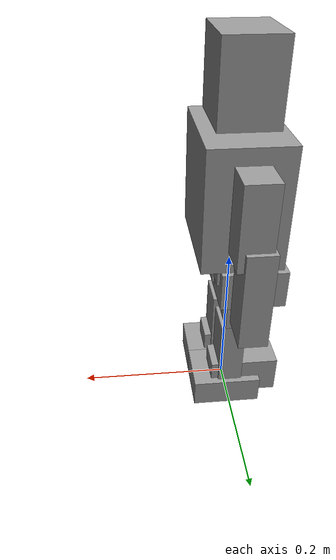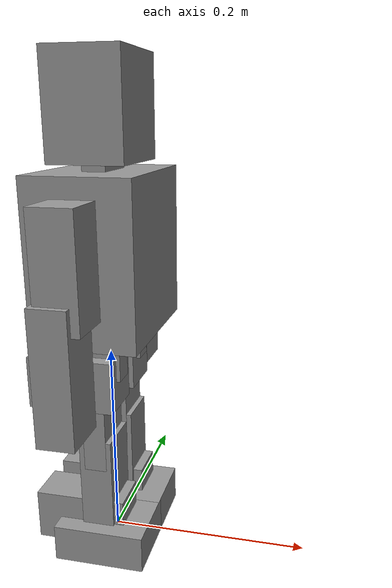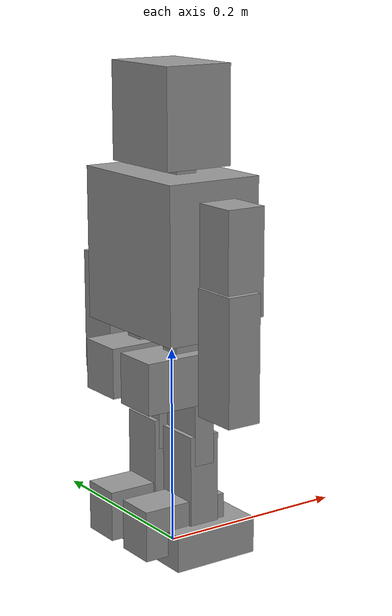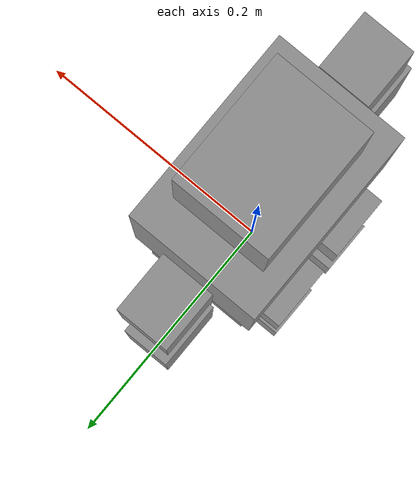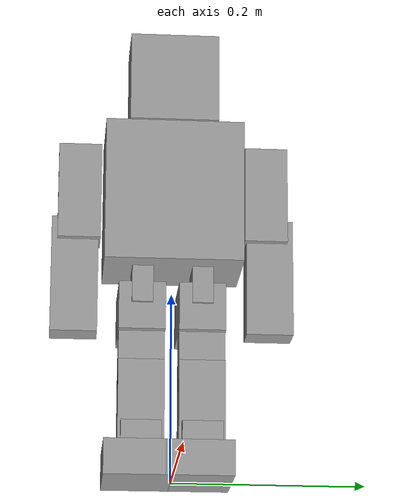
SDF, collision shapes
<?xml version='1.0'?>
<sdf version='1.6'>
  <model name='soccerbot'>
    <link name='torso'>
      <inertial>
        <mass>1</mass>
        <inertia>
          <ixx>0.003149</ixx>
          <ixy>0.000127</ixy>
          <ixz>0.000124</ixz>
          <iyy>0.004988</iyy>
          <iyz>8.9e-05</iyz>
          <izz>0.003395</izz>
        </inertia>
        <pose frame=''>0 0 0 0 -0 0</pose>
      </inertial>
      <pose frame=''>0 -0 0.301418 -0.037717 1.57079 1.53308</pose>
      <gravity>1</gravity>
      <self_collide>0</self_collide>
      <kinematic>0</kinematic>
      <enable_wind>0</enable_wind>
      <visual name='visual'>
        <pose frame=''>-0.076 -0.05 -0.0725 0 -0 0</pose>
        <geometry>
          <mesh>
            <uri>model://meshes/Torso.stl</uri>
            <scale>0.001 0.001 0.001</scale>
          </mesh>
        </geometry>
        <material>
          <lighting>1</lighting>
          <script>
            <uri>file://media/materials/scripts/gazebo.material</uri>
            <name>Gazebo/Grey</name>
          </script>
          <shader type='vertex'>
            <normal_map>__default__</normal_map>
          </shader>
          <ambient>0.3 0.3 0.3 1</ambient>
          <diffuse>0.7 0.7 0.7 1</diffuse>
          <specular>0.01 0.01 0.01 1</specular>
          <emissive>0 0 0 1</emissive>
        </material>
        <transparency>0</transparency>
        <cast_shadows>1</cast_shadows>
      </visual>
      <collision name='collision'>
        <laser_retro>0</laser_retro>
        <max_contacts>10</max_contacts>
        <pose frame=''>0 0 0 0 -0 0</pose>
        <geometry>
          <box>
            <size>0.152 0.1 0.145</size>
          </box>
        </geometry>
        <surface>
          <friction>
            <ode>
              <mu>1</mu>
              <mu2>1</mu2>
              <fdir1>0 0 0</fdir1>
              <slip1>0</slip1>
              <slip2>0</slip2>
            </ode>
            <torsional>
              <coefficient>1</coefficient>
              <patch_radius>0</patch_radius>
              <surface_radius>0</surface_radius>
              <use_patch_radius>1</use_patch_radius>
              <ode>
                <slip>0</slip>
              </ode>
            </torsional>
          </friction>
          <bounce>
            <restitution_coefficient>0</restitution_coefficient>
            <threshold>1e+06</threshold>
          </bounce>
          <contact>
            <collide_without_contact>0</collide_without_contact>
            <collide_without_contact_bitmask>1</collide_without_contact_bitmask>
            <collide_bitmask>1</collide_bitmask>
            <ode>
              <soft_cfm>0</soft_cfm>
              <soft_erp>0.2</soft_erp>
              <kp>1e+13</kp>
              <kd>1</kd>
              <max_vel>0.01</max_vel>
              <min_depth>0</min_depth>
            </ode>
            <bullet>
              <split_impulse>1</split_impulse>
              <split_impulse_penetration_threshold>-0.01</split_impulse_penetration_threshold>
              <soft_cfm>0</soft_cfm>
              <soft_erp>0.2</soft_erp>
              <kp>1e+13</kp>
              <kd>1</kd>
            </bullet>
          </contact>
        </surface>
      </collision>
    </link>
    <link name='camera'>
      <inertial>
        <mass>1</mass>
        <inertia>
          <ixx>0.166667</ixx>
          <ixy>0</ixy>
          <ixz>0</ixz>
          <iyy>0.166667</iyy>
          <iyz>0</iyz>
          <izz>0.166667</izz>
        </inertia>
        <pose frame=''>0 0 0 0 -0 0</pose>
      </inertial>
      <pose frame=''>0.1 -0 0.465818 0 -0 0</pose>
      <gravity>1</gravity>
      <self_collide>0</self_collide>
      <kinematic>0</kinematic>
      <enable_wind>0</enable_wind>
      <sensor name='camera1' type='camera'>
        <update_rate>30</update_rate>
        <camera name='__default__'>
          <horizontal_fov>1.39626</horizontal_fov>
          <image>
            <width>320</width>
            <height>240</height>
            <format>R8G8B8</format>
          </image>
          <clip>
            <near>1</near>
            <far>100</far>
          </clip>
          <noise>
            <type>gaussian</type>
            <mean>0</mean>
            <stddev>0.007</stddev>
          </noise>
        </camera>
        <always_on>1</always_on>
        <visualize>1</visualize>
        <plugin name='camera_controller' filename='libgazebo_ros_camera.so'>
          <alwaysOn>true</alwaysOn>
          <updateRate>0.0</updateRate>
          <cameraName>soccerbot/camera1</cameraName>
          <imageTopicName>image_raw</imageTopicName>
          <cameraInfoTopicName>camera_info</cameraInfoTopicName>
          <frameName>camera_link</frameName>
          <hackBaseline>0.07</hackBaseline>
          <distortionK1>0.0</distortionK1>
          <distortionK2>0.0</distortionK2>
          <distortionK3>0.0</distortionK3>
          <distortionT1>0.0</distortionT1>
          <distortionT2>0.0</distortionT2>
        </plugin>
      </sensor>
    </link>
    <link name='head'>
      <inertial>
        <mass>1</mass>
        <inertia>
          <ixx>0.166667</ixx>
          <ixy>0</ixy>
          <ixz>0</ixz>
          <iyy>0.166667</iyy>
          <iyz>0</iyz>
          <izz>0.166667</izz>
        </inertia>
        <pose frame=''>0 0 0 0 -0 0</pose>
      </inertial>
      <pose frame=''>0 -0 0.395918 1.5708 -0 1.5708</pose>
      <gravity>1</gravity>
      <self_collide>0</self_collide>
      <kinematic>0</kinematic>
      <enable_wind>0</enable_wind>
      <visual name='visual'>
        <pose frame=''>0 0 0 0 -0 0</pose>
        <geometry>
          <mesh>
            <uri>model://meshes/Head.stl</uri>
            <scale>0.001 0.001 0.001</scale>
          </mesh>
        </geometry>
        <material>
          <lighting>1</lighting>
          <script>
            <uri>file://media/materials/scripts/gazebo.material</uri>
            <name>Gazebo/Grey</name>
          </script>
          <shader type='vertex'>
            <normal_map>__default__</normal_map>
          </shader>
          <ambient>0.3 0.3 0.3 1</ambient>
          <diffuse>0.7 0.7 0.7 1</diffuse>
          <specular>0.01 0.01 0.01 1</specular>
          <emissive>0 0 0 1</emissive>
        </material>
        <transparency>0</transparency>
        <cast_shadows>1</cast_shadows>
      </visual>
      <collision name='collision'>
        <laser_retro>0</laser_retro>
        <max_contacts>10</max_contacts>
        <pose frame=''>0 0.03648 0 0 -0 0</pose>
        <geometry>
          <box>
            <size>0.094 0.09596 0.0712</size>
          </box>
        </geometry>
        <surface>
          <friction>
            <ode>
              <mu>1</mu>
              <mu2>1</mu2>
              <fdir1>0 0 0</fdir1>
              <slip1>0</slip1>
              <slip2>0</slip2>
            </ode>
            <torsional>
              <coefficient>1</coefficient>
              <patch_radius>0</patch_radius>
              <surface_radius>0</surface_radius>
              <use_patch_radius>1</use_patch_radius>
              <ode>
                <slip>0</slip>
              </ode>
            </torsional>
          </friction>
          <bounce>
            <restitution_coefficient>0</restitution_coefficient>
            <threshold>1e+06</threshold>
          </bounce>
          <contact>
            <collide_without_contact>0</collide_without_contact>
            <collide_without_contact_bitmask>1</collide_without_contact_bitmask>
            <collide_bitmask>1</collide_bitmask>
            <ode>
              <soft_cfm>0</soft_cfm>
              <soft_erp>0.2</soft_erp>
              <kp>1e+13</kp>
              <kd>1</kd>
              <max_vel>0.01</max_vel>
              <min_depth>0</min_depth>
            </ode>
            <bullet>
              <split_impulse>1</split_impulse>
              <split_impulse_penetration_threshold>-0.01</split_impulse_penetration_threshold>
              <soft_cfm>0</soft_cfm>
              <soft_erp>0.2</soft_erp>
              <kp>1e+13</kp>
              <kd>1</kd>
            </bullet>
          </contact>
        </surface>
      </collision>
    </link>
    <link name='left_ankle'>
      <inertial>
        <mass>1</mass>
        <inertia>
          <ixx>0.166667</ixx>
          <ixy>0</ixy>
          <ixz>0</ixz>
          <iyy>0.166667</iyy>
          <iyz>0</iyz>
          <izz>0.166667</izz>
        </inertia>
        <pose frame=''>0 0 0 1.57073 -0 0</pose>
      </inertial>
      <pose frame=''>0 -0.0315 0.025328 1.57073 -0 0</pose>
      <gravity>1</gravity>
      <self_collide>0</self_collide>
      <kinematic>0</kinematic>
      <enable_wind>0</enable_wind>
      <visual name='visual'>
        <pose frame=''>0 0 0 0 -0 0</pose>
        <geometry>
          <mesh>
            <uri>model://meshes/Left Ankle.stl</uri>
            <scale>0.001 0.001 0.001</scale>
          </mesh>
        </geometry>
        <material>
          <lighting>1</lighting>
          <script>
            <uri>file://media/materials/scripts/gazebo.material</uri>
            <name>Gazebo/Grey</name>
          </script>
          <shader type='vertex'>
            <normal_map>__default__</normal_map>
          </shader>
          <ambient>0.3 0.3 0.3 1</ambient>
          <diffuse>0.7 0.7 0.7 1</diffuse>
          <specular>0.01 0.01 0.01 1</specular>
          <emissive>0 0 0 1</emissive>
        </material>
        <transparency>0</transparency>
        <cast_shadows>1</cast_shadows>
      </visual>
      <collision name='collision'>
        <laser_retro>0</laser_retro>
        <max_contacts>10</max_contacts>
        <pose frame=''>-0.020145 0.01031 0 0 -0 0</pose>
        <geometry>
          <box>
            <size>0.090769 0.0506 0.042</size>
          </box>
        </geometry>
        <surface>
          <friction>
            <ode>
              <mu>1</mu>
              <mu2>1</mu2>
              <fdir1>0 0 0</fdir1>
              <slip1>0</slip1>
              <slip2>0</slip2>
            </ode>
            <torsional>
              <coefficient>1</coefficient>
              <patch_radius>0</patch_radius>
              <surface_radius>0</surface_radius>
              <use_patch_radius>1</use_patch_radius>
              <ode>
                <slip>0</slip>
              </ode>
            </torsional>
          </friction>
          <bounce>
            <restitution_coefficient>0</restitution_coefficient>
            <threshold>1e+06</threshold>
          </bounce>
          <contact>
            <collide_without_contact>0</collide_without_contact>
            <collide_without_contact_bitmask>1</collide_without_contact_bitmask>
            <collide_bitmask>1</collide_bitmask>
            <ode>
              <soft_cfm>0</soft_cfm>
              <soft_erp>0.2</soft_erp>
              <kp>1e+13</kp>
              <kd>1</kd>
              <max_vel>0.01</max_vel>
              <min_depth>0</min_depth>
            </ode>
            <bullet>
              <split_impulse>1</split_impulse>
              <split_impulse_penetration_threshold>-0.01</split_impulse_penetration_threshold>
              <soft_cfm>0</soft_cfm>
              <soft_erp>0.2</soft_erp>
              <kp>1e+13</kp>
              <kd>1</kd>
            </bullet>
          </contact>
        </surface>
      </collision>
    </link>
    <link name='left_bicep'>
      <inertial>
        <mass>1</mass>
        <inertia>
          <ixx>0.166667</ixx>
          <ixy>0</ixy>
          <ixz>0</ixz>
          <iyy>0.166667</iyy>
          <iyz>0</iyz>
          <izz>0.166667</izz>
        </inertia>
        <pose frame=''>0 0 0 0 -0 0</pose>
      </inertial>
      <pose frame=''>0 -0.076 0.347678 1.5708 -0 0</pose>
      <gravity>1</gravity>
      <self_collide>0</self_collide>
      <kinematic>0</kinematic>
      <enable_wind>0</enable_wind>
      <visual name='visual'>
        <pose frame=''>0 0 0 0 -0 0</pose>
        <geometry>
          <mesh>
            <uri>model://meshes/Left Bicep.stl</uri>
            <scale>0.001 0.001 0.001</scale>
          </mesh>
        </geometry>
        <material>
          <lighting>1</lighting>
          <script>
            <uri>file://media/materials/scripts/gazebo.material</uri>
            <name>Gazebo/Grey</name>
          </script>
          <shader type='vertex'>
            <normal_map>__default__</normal_map>
          </shader>
          <ambient>0.3 0.3 0.3 1</ambient>
          <diffuse>0.7 0.7 0.7 1</diffuse>
          <specular>0.01 0.01 0.01 1</specular>
          <emissive>0 0 0 1</emissive>
        </material>
        <transparency>0</transparency>
        <cast_shadows>1</cast_shadows>
      </visual>
      <collision name='collision'>
        <laser_retro>0</laser_retro>
        <max_contacts>10</max_contacts>
        <pose frame=''>0 -0.04 0.0225 0 -0 0</pose>
        <geometry>
          <box>
            <size>0.04 0.103 0.045</size>
          </box>
        </geometry>
        <surface>
          <friction>
            <ode>
              <mu>1</mu>
              <mu2>1</mu2>
              <fdir1>0 0 0</fdir1>
              <slip1>0</slip1>
              <slip2>0</slip2>
            </ode>
            <torsional>
              <coefficient>1</coefficient>
              <patch_radius>0</patch_radius>
              <surface_radius>0</surface_radius>
              <use_patch_radius>1</use_patch_radius>
              <ode>
                <slip>0</slip>
              </ode>
            </torsional>
          </friction>
          <bounce>
            <restitution_coefficient>0</restitution_coefficient>
            <threshold>1e+06</threshold>
          </bounce>
          <contact>
            <collide_without_contact>0</collide_without_contact>
            <collide_without_contact_bitmask>1</collide_without_contact_bitmask>
            <collide_bitmask>1</collide_bitmask>
            <ode>
              <soft_cfm>0</soft_cfm>
              <soft_erp>0.2</soft_erp>
              <kp>1e+13</kp>
              <kd>1</kd>
              <max_vel>0.01</max_vel>
              <min_depth>0</min_depth>
            </ode>
            <bullet>
              <split_impulse>1</split_impulse>
              <split_impulse_penetration_threshold>-0.01</split_impulse_penetration_threshold>
              <soft_cfm>0</soft_cfm>
              <soft_erp>0.2</soft_erp>
              <kp>1e+13</kp>
              <kd>1</kd>
            </bullet>
          </contact>
        </surface>
      </collision>
    </link>
    <link name='left_calve'>
      <inertial>
        <mass>1</mass>
        <inertia>
          <ixx>0.166667</ixx>
          <ixy>0</ixy>
          <ixz>0</ixz>
          <iyy>0.166667</iyy>
          <iyz>0</iyz>
          <izz>0.166667</izz>
        </inertia>
        <pose frame=''>0 0 0 0 -0 0</pose>
      </inertial>
      <pose frame=''>0 -0.0315 0.025328 1.57079 -0 0</pose>
      <gravity>1</gravity>
      <self_collide>0</self_collide>
      <kinematic>0</kinematic>
      <enable_wind>0</enable_wind>
      <visual name='visual'>
        <pose frame=''>0 0 0 0 -0 0</pose>
        <geometry>
          <mesh>
            <uri>model://meshes/Left Calve.stl</uri>
            <scale>0.001 0.001 0.001</scale>
          </mesh>
        </geometry>
        <material>
          <lighting>1</lighting>
          <script>
            <uri>file://media/materials/scripts/gazebo.material</uri>
            <name>Gazebo/Grey</name>
          </script>
          <shader type='vertex'>
            <normal_map>__default__</normal_map>
          </shader>
          <ambient>0.3 0.3 0.3 1</ambient>
          <diffuse>0.7 0.7 0.7 1</diffuse>
          <specular>0.01 0.01 0.01 1</specular>
          <emissive>0 0 0 1</emissive>
        </material>
        <transparency>0</transparency>
        <cast_shadows>1</cast_shadows>
      </visual>
      <collision name='collision'>
        <laser_retro>0</laser_retro>
        <max_contacts>10</max_contacts>
        <pose frame=''>0 0.04885 0 0 -0 0</pose>
        <geometry>
          <box>
            <size>0.031883 0.105683 0.048</size>
          </box>
        </geometry>
        <surface>
          <friction>
            <ode>
              <mu>1</mu>
              <mu2>1</mu2>
              <fdir1>0 0 0</fdir1>
              <slip1>0</slip1>
              <slip2>0</slip2>
            </ode>
            <torsional>
              <coefficient>1</coefficient>
              <patch_radius>0</patch_radius>
              <surface_radius>0</surface_radius>
              <use_patch_radius>1</use_patch_radius>
              <ode>
                <slip>0</slip>
              </ode>
            </torsional>
          </friction>
          <bounce>
            <restitution_coefficient>0</restitution_coefficient>
            <threshold>1e+06</threshold>
          </bounce>
          <contact>
            <collide_without_contact>0</collide_without_contact>
            <collide_without_contact_bitmask>1</collide_without_contact_bitmask>
            <collide_bitmask>1</collide_bitmask>
            <ode>
              <soft_cfm>0</soft_cfm>
              <soft_erp>0.2</soft_erp>
              <kp>1e+13</kp>
              <kd>1</kd>
              <max_vel>0.01</max_vel>
              <min_depth>0</min_depth>
            </ode>
            <bullet>
              <split_impulse>1</split_impulse>
              <split_impulse_penetration_threshold>-0.01</split_impulse_penetration_threshold>
              <soft_cfm>0</soft_cfm>
              <soft_erp>0.2</soft_erp>
              <kp>1e+13</kp>
              <kd>1</kd>
            </bullet>
          </contact>
        </surface>
      </collision>
    </link>
    <link name='left_foot'>
      <inertial>
        <mass>1</mass>
        <inertia>
          <ixx>0.166667</ixx>
          <ixy>0</ixy>
          <ixz>0</ixz>
          <iyy>0.166667</iyy>
          <iyz>0</iyz>
          <izz>0.166667</izz>
        </inertia>
        <pose frame=''>0 0 0 1.57073 -0 0</pose>
      </inertial>
      <pose frame=''>0 -0.0315 0.025328 1.57073 -0 0</pose>
      <gravity>1</gravity>
      <self_collide>0</self_collide>
      <kinematic>0</kinematic>
      <enable_wind>0</enable_wind>
      <visual name='visual'>
        <pose frame=''>0 0 0 0 -0 0</pose>
        <geometry>
          <mesh>
            <uri>model://meshes/Left Foot.stl</uri>
            <scale>0.001 0.001 0.001</scale>
          </mesh>
        </geometry>
        <material>
          <lighting>1</lighting>
          <script>
            <uri>file://media/materials/scripts/gazebo.material</uri>
            <name>Gazebo/Grey</name>
          </script>
          <shader type='vertex'>
            <normal_map>__default__</normal_map>
          </shader>
          <ambient>0.3 0.3 0.3 1</ambient>
          <diffuse>0.7 0.7 0.7 1</diffuse>
          <specular>0.01 0.01 0.01 1</specular>
          <emissive>0 0 0 1</emissive>
        </material>
        <transparency>0</transparency>
        <cast_shadows>1</cast_shadows>
      </visual>
      <collision name='collision'>
        <laser_retro>0</laser_retro>
        <max_contacts>10</max_contacts>
        <pose frame=''>0.004015 -0.00737 0.00385 0 -0 0</pose>
        <geometry>
          <box>
            <size>0.09 0.03674 0.07</size>
          </box>
        </geometry>
        <surface>
          <friction>
            <ode>
              <mu>1</mu>
              <mu2>1</mu2>
              <fdir1>0 0 0</fdir1>
              <slip1>0</slip1>
              <slip2>0</slip2>
            </ode>
            <torsional>
              <coefficient>1</coefficient>
              <patch_radius>0</patch_radius>
              <surface_radius>0</surface_radius>
              <use_patch_radius>1</use_patch_radius>
              <ode>
                <slip>0</slip>
              </ode>
            </torsional>
          </friction>
          <bounce>
            <restitution_coefficient>0</restitution_coefficient>
            <threshold>1e+06</threshold>
          </bounce>
          <contact>
            <collide_without_contact>0</collide_without_contact>
            <collide_without_contact_bitmask>1</collide_without_contact_bitmask>
            <collide_bitmask>1</collide_bitmask>
            <ode>
              <soft_cfm>0</soft_cfm>
              <soft_erp>0.2</soft_erp>
              <kp>1e+13</kp>
              <kd>1</kd>
              <max_vel>0.01</max_vel>
              <min_depth>0</min_depth>
            </ode>
            <bullet>
              <split_impulse>1</split_impulse>
              <split_impulse_penetration_threshold>-0.01</split_impulse_penetration_threshold>
              <soft_cfm>0</soft_cfm>
              <soft_erp>0.2</soft_erp>
              <kp>1e+13</kp>
              <kd>1</kd>
            </bullet>
          </contact>
        </surface>
      </collision>
    </link>
    <link name='left_forearm'>
      <inertial>
        <mass>1</mass>
        <inertia>
          <ixx>0.166667</ixx>
          <ixy>0</ixy>
          <ixz>0</ixz>
          <iyy>0.166667</iyy>
          <iyz>0</iyz>
          <izz>0.166667</izz>
        </inertia>
        <pose frame=''>0 0 0 0 -0 0</pose>
      </inertial>
      <pose frame=''>0 -0.076 0.267678 1.5708 -0 0</pose>
      <gravity>1</gravity>
      <self_collide>0</self_collide>
      <kinematic>0</kinematic>
      <enable_wind>0</enable_wind>
      <visual name='visual'>
        <pose frame=''>0 0 0 0 -0 0</pose>
        <geometry>
          <mesh>
            <uri>model://meshes/Left Forearm.stl</uri>
            <scale>0.001 0.001 0.001</scale>
          </mesh>
        </geometry>
        <material>
          <lighting>1</lighting>
          <script>
            <uri>file://media/materials/scripts/gazebo.material</uri>
            <name>Gazebo/Grey</name>
          </script>
          <shader type='vertex'>
            <normal_map>__default__</normal_map>
          </shader>
          <ambient>0.3 0.3 0.3 1</ambient>
          <diffuse>0.7 0.7 0.7 1</diffuse>
          <specular>0.01 0.01 0.01 1</specular>
          <emissive>0 0 0 1</emissive>
        </material>
        <transparency>0</transparency>
        <cast_shadows>1</cast_shadows>
      </visual>
      <collision name='collision'>
        <laser_retro>0</laser_retro>
        <max_contacts>10</max_contacts>
        <pose frame=''>-0.0055 -0.049 0.0265 0 -0 0</pose>
        <geometry>
          <box>
            <size>0.035 0.124 0.049</size>
          </box>
        </geometry>
        <surface>
          <friction>
            <ode>
              <mu>1</mu>
              <mu2>1</mu2>
              <fdir1>0 0 0</fdir1>
              <slip1>0</slip1>
              <slip2>0</slip2>
            </ode>
            <torsional>
              <coefficient>1</coefficient>
              <patch_radius>0</patch_radius>
              <surface_radius>0</surface_radius>
              <use_patch_radius>1</use_patch_radius>
              <ode>
                <slip>0</slip>
              </ode>
            </torsional>
          </friction>
          <bounce>
            <restitution_coefficient>0</restitution_coefficient>
            <threshold>1e+06</threshold>
          </bounce>
          <contact>
            <collide_without_contact>0</collide_without_contact>
            <collide_without_contact_bitmask>1</collide_without_contact_bitmask>
            <collide_bitmask>1</collide_bitmask>
            <ode>
              <soft_cfm>0</soft_cfm>
              <soft_erp>0.2</soft_erp>
              <kp>1e+13</kp>
              <kd>1</kd>
              <max_vel>0.01</max_vel>
              <min_depth>0</min_depth>
            </ode>
            <bullet>
              <split_impulse>1</split_impulse>
              <split_impulse_penetration_threshold>-0.01</split_impulse_penetration_threshold>
              <soft_cfm>0</soft_cfm>
              <soft_erp>0.2</soft_erp>
              <kp>1e+13</kp>
              <kd>1</kd>
            </bullet>
          </contact>
        </surface>
      </collision>
    </link>
    <link name='left_hip_front'>
      <inertial>
        <mass>1</mass>
        <inertia>
          <ixx>0.166667</ixx>
          <ixy>0</ixy>
          <ixz>0</ixz>
          <iyy>0.166667</iyy>
          <iyz>0</iyz>
          <izz>0.166667</izz>
        </inertia>
        <pose frame=''>0 0 0 0 -0 0</pose>
      </inertial>
      <pose frame=''>0 -0.0315 0.197 1.57079 -0 0</pose>
      <gravity>1</gravity>
      <self_collide>0</self_collide>
      <kinematic>0</kinematic>
      <enable_wind>0</enable_wind>
      <visual name='visual'>
        <pose frame=''>0 0 0 0 -0 0</pose>
        <geometry>
          <mesh>
            <uri>model://meshes/Left Hip Front.stl</uri>
            <scale>0.001 0.001 0.001</scale>
          </mesh>
        </geometry>
        <material>
          <lighting>1</lighting>
          <script>
            <uri>file://media/materials/scripts/gazebo.material</uri>
            <name>Gazebo/Grey</name>
          </script>
          <shader type='vertex'>
            <normal_map>__default__</normal_map>
          </shader>
          <ambient>0.3 0.3 0.3 1</ambient>
          <diffuse>0.7 0.7 0.7 1</diffuse>
          <specular>0.01 0.01 0.01 1</specular>
          <emissive>0 0 0 1</emissive>
        </material>
        <transparency>0</transparency>
        <cast_shadows>1</cast_shadows>
      </visual>
      <collision name='collision'>
        <laser_retro>0</laser_retro>
        <max_contacts>10</max_contacts>
        <pose frame=''>-0.02187 -0.013322 0 0 -0 0</pose>
        <geometry>
          <box>
            <size>0.083747 0.0506 0.04885</size>
          </box>
        </geometry>
        <surface>
          <friction>
            <ode>
              <mu>1</mu>
              <mu2>1</mu2>
              <fdir1>0 0 0</fdir1>
              <slip1>0</slip1>
              <slip2>0</slip2>
            </ode>
            <torsional>
              <coefficient>1</coefficient>
              <patch_radius>0</patch_radius>
              <surface_radius>0</surface_radius>
              <use_patch_radius>1</use_patch_radius>
              <ode>
                <slip>0</slip>
              </ode>
            </torsional>
          </friction>
          <bounce>
            <restitution_coefficient>0</restitution_coefficient>
            <threshold>1e+06</threshold>
          </bounce>
          <contact>
            <collide_without_contact>0</collide_without_contact>
            <collide_without_contact_bitmask>1</collide_without_contact_bitmask>
            <collide_bitmask>1</collide_bitmask>
            <ode>
              <soft_cfm>0</soft_cfm>
              <soft_erp>0.2</soft_erp>
              <kp>1e+13</kp>
              <kd>1</kd>
              <max_vel>0.01</max_vel>
              <min_depth>0</min_depth>
            </ode>
            <bullet>
              <split_impulse>1</split_impulse>
              <split_impulse_penetration_threshold>-0.01</split_impulse_penetration_threshold>
              <soft_cfm>0</soft_cfm>
              <soft_erp>0.2</soft_erp>
              <kp>1e+13</kp>
              <kd>1</kd>
            </bullet>
          </contact>
        </surface>
      </collision>
    </link>
    <link name='left_hip_side'>
      <inertial>
        <mass>1</mass>
        <inertia>
          <ixx>0.166667</ixx>
          <ixy>0</ixy>
          <ixz>0</ixz>
          <iyy>0.166667</iyy>
          <iyz>0</iyz>
          <izz>0.166667</izz>
        </inertia>
        <pose frame=''>0 0 0 0 -0 0</pose>
      </inertial>
      <pose frame=''>0 -0.031494 0.197 1.5708 -0 1.5708</pose>
      <gravity>1</gravity>
      <self_collide>0</self_collide>
      <kinematic>0</kinematic>
      <enable_wind>0</enable_wind>
      <visual name='visual'>
        <pose frame=''>0 0 0 0 -0 0</pose>
        <geometry>
          <mesh>
            <uri>model://meshes/Left Hip Side.stl</uri>
            <scale>0.001 0.001 0.001</scale>
          </mesh>
        </geometry>
        <material>
          <lighting>1</lighting>
          <script>
            <uri>file://media/materials/scripts/gazebo.material</uri>
            <name>Gazebo/Grey</name>
          </script>
          <shader type='vertex'>
            <normal_map>__default__</normal_map>
          </shader>
          <ambient>0.3 0.3 0.3 1</ambient>
          <diffuse>0.7 0.7 0.7 1</diffuse>
          <specular>0.01 0.01 0.01 1</specular>
          <emissive>0 0 0 1</emissive>
        </material>
        <transparency>0</transparency>
        <cast_shadows>1</cast_shadows>
      </visual>
      <collision name='collision'>
        <laser_retro>0</laser_retro>
        <max_contacts>10</max_contacts>
        <pose frame=''>0 0.009 0 0 -0 0</pose>
        <geometry>
          <box>
            <size>0.022 0.039 0.0475</size>
          </box>
        </geometry>
        <surface>
          <friction>
            <ode>
              <mu>1</mu>
              <mu2>1</mu2>
              <fdir1>0 0 0</fdir1>
              <slip1>0</slip1>
              <slip2>0</slip2>
            </ode>
            <torsional>
              <coefficient>1</coefficient>
              <patch_radius>0</patch_radius>
              <surface_radius>0</surface_radius>
              <use_patch_radius>1</use_patch_radius>
              <ode>
                <slip>0</slip>
              </ode>
            </torsional>
          </friction>
          <bounce>
            <restitution_coefficient>0</restitution_coefficient>
            <threshold>1e+06</threshold>
          </bounce>
          <contact>
            <collide_without_contact>0</collide_without_contact>
            <collide_without_contact_bitmask>1</collide_without_contact_bitmask>
            <collide_bitmask>1</collide_bitmask>
            <ode>
              <soft_cfm>0</soft_cfm>
              <soft_erp>0.2</soft_erp>
              <kp>1e+13</kp>
              <kd>1</kd>
              <max_vel>0.01</max_vel>
              <min_depth>0</min_depth>
            </ode>
            <bullet>
              <split_impulse>1</split_impulse>
              <split_impulse_penetration_threshold>-0.01</split_impulse_penetration_threshold>
              <soft_cfm>0</soft_cfm>
              <soft_erp>0.2</soft_erp>
              <kp>1e+13</kp>
              <kd>1</kd>
            </bullet>
          </contact>
        </surface>
      </collision>
    </link>
    <link name='left_thigh'>
      <inertial>
        <mass>1</mass>
        <inertia>
          <ixx>0.166667</ixx>
          <ixy>0</ixy>
          <ixz>0</ixz>
          <iyy>0.166667</iyy>
          <iyz>0</iyz>
          <izz>0.166667</izz>
        </inertia>
        <pose frame=''>0 0 0 0 -0 0</pose>
      </inertial>
      <pose frame=''>0 -0.0315 0.197 1.5708 -0 0</pose>
      <gravity>1</gravity>
      <self_collide>0</self_collide>
      <kinematic>0</kinematic>
      <enable_wind>0</enable_wind>
      <visual name='visual'>
        <pose frame=''>0 0 0 0 -0 0</pose>
        <geometry>
          <mesh>
            <uri>model://meshes/Left Thigh.stl</uri>
            <scale>0.001 0.001 0.001</scale>
          </mesh>
        </geometry>
        <material>
          <lighting>1</lighting>
          <script>
            <uri>file://media/materials/scripts/gazebo.material</uri>
            <name>Gazebo/Grey</name>
          </script>
          <shader type='vertex'>
            <normal_map>__default__</normal_map>
          </shader>
          <ambient>0.3 0.3 0.3 1</ambient>
          <diffuse>0.7 0.7 0.7 1</diffuse>
          <specular>0.01 0.01 0.01 1</specular>
          <emissive>0 0 0 1</emissive>
        </material>
        <transparency>0</transparency>
        <cast_shadows>1</cast_shadows>
      </visual>
      <collision name='collision'>
        <laser_retro>0</laser_retro>
        <max_contacts>10</max_contacts>
        <pose frame=''>0 -0.0445 0 0 -0 0</pose>
        <geometry>
          <box>
            <size>0.022 0.111 0.048</size>
          </box>
        </geometry>
        <surface>
          <friction>
            <ode>
              <mu>1</mu>
              <mu2>1</mu2>
              <fdir1>0 0 0</fdir1>
              <slip1>0</slip1>
              <slip2>0</slip2>
            </ode>
            <torsional>
              <coefficient>1</coefficient>
              <patch_radius>0</patch_radius>
              <surface_radius>0</surface_radius>
              <use_patch_radius>1</use_patch_radius>
              <ode>
                <slip>0</slip>
              </ode>
            </torsional>
          </friction>
          <bounce>
            <restitution_coefficient>0</restitution_coefficient>
            <threshold>1e+06</threshold>
          </bounce>
          <contact>
            <collide_without_contact>0</collide_without_contact>
            <collide_without_contact_bitmask>1</collide_without_contact_bitmask>
            <collide_bitmask>1</collide_bitmask>
            <ode>
              <soft_cfm>0</soft_cfm>
              <soft_erp>0.2</soft_erp>
              <kp>1e+13</kp>
              <kd>1</kd>
              <max_vel>0.01</max_vel>
              <min_depth>0</min_depth>
            </ode>
            <bullet>
              <split_impulse>1</split_impulse>
              <split_impulse_penetration_threshold>-0.01</split_impulse_penetration_threshold>
              <soft_cfm>0</soft_cfm>
              <soft_erp>0.2</soft_erp>
              <kp>1e+13</kp>
              <kd>1</kd>
            </bullet>
          </contact>
        </surface>
      </collision>
    </link>
    <link name='neck'>
      <inertial>
        <mass>1</mass>
        <inertia>
          <ixx>0.166667</ixx>
          <ixy>0</ixy>
          <ixz>0</ixz>
          <iyy>0.166667</iyy>
          <iyz>0</iyz>
          <izz>0.166667</izz>
        </inertia>
        <pose frame=''>0 0 0 0 -0 0</pose>
      </inertial>
      <pose frame=''>0 -0 0.373918 1.57079 -0 1.57079</pose>
      <gravity>1</gravity>
      <self_collide>0</self_collide>
      <kinematic>0</kinematic>
      <enable_wind>0</enable_wind>
      <visual name='visual'>
        <pose frame=''>0 0 0 0 -0 0</pose>
        <geometry>
          <mesh>
            <uri>model://meshes/Neck.stl</uri>
            <scale>0.001 0.001 0.001</scale>
          </mesh>
        </geometry>
        <material>
          <lighting>1</lighting>
          <script>
            <uri>file://media/materials/scripts/gazebo.material</uri>
            <name>Gazebo/Grey</name>
          </script>
          <shader type='vertex'>
            <normal_map>__default__</normal_map>
          </shader>
          <ambient>0.3 0.3 0.3 1</ambient>
          <diffuse>0.7 0.7 0.7 1</diffuse>
          <specular>0.01 0.01 0.01 1</specular>
          <emissive>0 0 0 1</emissive>
        </material>
        <transparency>0</transparency>
        <cast_shadows>1</cast_shadows>
      </visual>
      <collision name='collision'>
        <laser_retro>0</laser_retro>
        <max_contacts>10</max_contacts>
        <pose frame=''>0 0.0165 0 0 -0 0</pose>
        <geometry>
          <box>
            <size>0.0523 0.033 0.022</size>
          </box>
        </geometry>
        <surface>
          <friction>
            <ode>
              <mu>1</mu>
              <mu2>1</mu2>
              <fdir1>0 0 0</fdir1>
              <slip1>0</slip1>
              <slip2>0</slip2>
            </ode>
            <torsional>
              <coefficient>1</coefficient>
              <patch_radius>0</patch_radius>
              <surface_radius>0</surface_radius>
              <use_patch_radius>1</use_patch_radius>
              <ode>
                <slip>0</slip>
              </ode>
            </torsional>
          </friction>
          <bounce>
            <restitution_coefficient>0</restitution_coefficient>
            <threshold>1e+06</threshold>
          </bounce>
          <contact>
            <collide_without_contact>0</collide_without_contact>
            <collide_without_contact_bitmask>1</collide_without_contact_bitmask>
            <collide_bitmask>1</collide_bitmask>
            <ode>
              <soft_cfm>0</soft_cfm>
              <soft_erp>0.2</soft_erp>
              <kp>1e+13</kp>
              <kd>1</kd>
              <max_vel>0.01</max_vel>
              <min_depth>0</min_depth>
            </ode>
            <bullet>
              <split_impulse>1</split_impulse>
              <split_impulse_penetration_threshold>-0.01</split_impulse_penetration_threshold>
              <soft_cfm>0</soft_cfm>
              <soft_erp>0.2</soft_erp>
              <kp>1e+13</kp>
              <kd>1</kd>
            </bullet>
          </contact>
        </surface>
      </collision>
    </link>
    <link name='right_ankle'>
      <inertial>
        <mass>1</mass>
        <inertia>
          <ixx>0.166667</ixx>
          <ixy>0</ixy>
          <ixz>0</ixz>
          <iyy>0.166667</iyy>
          <iyz>0</iyz>
          <izz>0.166667</izz>
        </inertia>
        <pose frame=''>0 0 0 1.57073 -0 0</pose>
      </inertial>
      <pose frame=''>0 0.031494 0.025328 1.57073 -0 0</pose>
      <gravity>1</gravity>
      <self_collide>0</self_collide>
      <kinematic>0</kinematic>
      <enable_wind>0</enable_wind>
      <visual name='visual'>
        <pose frame=''>0 0 0 0 -0 0</pose>
        <geometry>
          <mesh>
            <uri>model://meshes/Right Ankle.stl</uri>
            <scale>0.001 0.001 0.001</scale>
          </mesh>
        </geometry>
        <material>
          <lighting>1</lighting>
          <script>
            <uri>file://media/materials/scripts/gazebo.material</uri>
            <name>Gazebo/Grey</name>
          </script>
          <shader type='vertex'>
            <normal_map>__default__</normal_map>
          </shader>
          <ambient>0.3 0.3 0.3 1</ambient>
          <diffuse>0.7 0.7 0.7 1</diffuse>
          <specular>0.01 0.01 0.01 1</specular>
          <emissive>0 0 0 1</emissive>
        </material>
        <transparency>0</transparency>
        <cast_shadows>1</cast_shadows>
      </visual>
      <collision name='collision'>
        <laser_retro>0</laser_retro>
        <max_contacts>10</max_contacts>
        <pose frame=''>-0.020145 0.01031 0 0 -0 0</pose>
        <geometry>
          <box>
            <size>0.090769 0.0506 0.042</size>
          </box>
        </geometry>
        <surface>
          <friction>
            <ode>
              <mu>1</mu>
              <mu2>1</mu2>
              <fdir1>0 0 0</fdir1>
              <slip1>0</slip1>
              <slip2>0</slip2>
            </ode>
            <torsional>
              <coefficient>1</coefficient>
              <patch_radius>0</patch_radius>
              <surface_radius>0</surface_radius>
              <use_patch_radius>1</use_patch_radius>
              <ode>
                <slip>0</slip>
              </ode>
            </torsional>
          </friction>
          <bounce>
            <restitution_coefficient>0</restitution_coefficient>
            <threshold>1e+06</threshold>
          </bounce>
          <contact>
            <collide_without_contact>0</collide_without_contact>
            <collide_without_contact_bitmask>1</collide_without_contact_bitmask>
            <collide_bitmask>1</collide_bitmask>
            <ode>
              <soft_cfm>0</soft_cfm>
              <soft_erp>0.2</soft_erp>
              <kp>1e+13</kp>
              <kd>1</kd>
              <max_vel>0.01</max_vel>
              <min_depth>0</min_depth>
            </ode>
            <bullet>
              <split_impulse>1</split_impulse>
              <split_impulse_penetration_threshold>-0.01</split_impulse_penetration_threshold>
              <soft_cfm>0</soft_cfm>
              <soft_erp>0.2</soft_erp>
              <kp>1e+13</kp>
              <kd>1</kd>
            </bullet>
          </contact>
        </surface>
      </collision>
    </link>
    <link name='right_bicep'>
      <inertial>
        <mass>1</mass>
        <inertia>
          <ixx>0.166667</ixx>
          <ixy>0</ixy>
          <ixz>0</ixz>
          <iyy>0.166667</iyy>
          <iyz>0</iyz>
          <izz>0.166667</izz>
        </inertia>
        <pose frame=''>0 0 0 0 -0 0</pose>
      </inertial>
      <pose frame=''>0 0.076 0.347678 1.5708 -0 0</pose>
      <gravity>1</gravity>
      <self_collide>0</self_collide>
      <kinematic>0</kinematic>
      <enable_wind>0</enable_wind>
      <visual name='visual'>
        <pose frame=''>0 0 0 0 -0 0</pose>
        <geometry>
          <mesh>
            <uri>model://meshes/Right Bicep.stl</uri>
            <scale>0.001 0.001 0.001</scale>
          </mesh>
        </geometry>
        <material>
          <lighting>1</lighting>
          <script>
            <uri>file://media/materials/scripts/gazebo.material</uri>
            <name>Gazebo/Grey</name>
          </script>
          <shader type='vertex'>
            <normal_map>__default__</normal_map>
          </shader>
          <ambient>0.3 0.3 0.3 1</ambient>
          <diffuse>0.7 0.7 0.7 1</diffuse>
          <specular>0.01 0.01 0.01 1</specular>
          <emissive>0 0 0 1</emissive>
        </material>
        <transparency>0</transparency>
        <cast_shadows>1</cast_shadows>
      </visual>
      <collision name='collision'>
        <laser_retro>0</laser_retro>
        <max_contacts>10</max_contacts>
        <pose frame=''>0 -0.04 -0.0225 0 -0 0</pose>
        <geometry>
          <box>
            <size>0.04 0.103 0.045</size>
          </box>
        </geometry>
        <surface>
          <friction>
            <ode>
              <mu>1</mu>
              <mu2>1</mu2>
              <fdir1>0 0 0</fdir1>
              <slip1>0</slip1>
              <slip2>0</slip2>
            </ode>
            <torsional>
              <coefficient>1</coefficient>
              <patch_radius>0</patch_radius>
              <surface_radius>0</surface_radius>
              <use_patch_radius>1</use_patch_radius>
              <ode>
                <slip>0</slip>
              </ode>
            </torsional>
          </friction>
          <bounce>
            <restitution_coefficient>0</restitution_coefficient>
            <threshold>1e+06</threshold>
          </bounce>
          <contact>
            <collide_without_contact>0</collide_without_contact>
            <collide_without_contact_bitmask>1</collide_without_contact_bitmask>
            <collide_bitmask>1</collide_bitmask>
            <ode>
              <soft_cfm>0</soft_cfm>
              <soft_erp>0.2</soft_erp>
              <kp>1e+13</kp>
              <kd>1</kd>
              <max_vel>0.01</max_vel>
              <min_depth>0</min_depth>
            </ode>
            <bullet>
              <split_impulse>1</split_impulse>
              <split_impulse_penetration_threshold>-0.01</split_impulse_penetration_threshold>
              <soft_cfm>0</soft_cfm>
              <soft_erp>0.2</soft_erp>
              <kp>1e+13</kp>
              <kd>1</kd>
            </bullet>
          </contact>
        </surface>
      </collision>
    </link>
    <link name='right_calve'>
      <inertial>
        <mass>1</mass>
        <inertia>
          <ixx>0.166667</ixx>
          <ixy>0</ixy>
          <ixz>0</ixz>
          <iyy>0.166667</iyy>
          <iyz>0</iyz>
          <izz>0.166667</izz>
        </inertia>
        <pose frame=''>0 0 0 0 -0 0</pose>
      </inertial>
      <pose frame=''>0 0.031494 0.025328 1.57079 -0 0</pose>
      <gravity>1</gravity>
      <self_collide>0</self_collide>
      <kinematic>0</kinematic>
      <enable_wind>0</enable_wind>
      <visual name='visual'>
        <pose frame=''>0 0 0 0 -0 0</pose>
        <geometry>
          <mesh>
            <uri>model://meshes/Right Calve.stl</uri>
            <scale>0.001 0.001 0.001</scale>
          </mesh>
        </geometry>
        <material>
          <lighting>1</lighting>
          <script>
            <uri>file://media/materials/scripts/gazebo.material</uri>
            <name>Gazebo/Grey</name>
          </script>
          <shader type='vertex'>
            <normal_map>__default__</normal_map>
          </shader>
          <ambient>0.3 0.3 0.3 1</ambient>
          <diffuse>0.7 0.7 0.7 1</diffuse>
          <specular>0.01 0.01 0.01 1</specular>
          <emissive>0 0 0 1</emissive>
        </material>
        <transparency>0</transparency>
        <cast_shadows>1</cast_shadows>
      </visual>
      <collision name='collision'>
        <laser_retro>0</laser_retro>
        <max_contacts>10</max_contacts>
        <pose frame=''>0 0.04885 0 0 -0 0</pose>
        <geometry>
          <box>
            <size>0.031883 0.105683 0.048</size>
          </box>
        </geometry>
        <surface>
          <friction>
            <ode>
              <mu>1</mu>
              <mu2>1</mu2>
              <fdir1>0 0 0</fdir1>
              <slip1>0</slip1>
              <slip2>0</slip2>
            </ode>
            <torsional>
              <coefficient>1</coefficient>
              <patch_radius>0</patch_radius>
              <surface_radius>0</surface_radius>
              <use_patch_radius>1</use_patch_radius>
              <ode>
                <slip>0</slip>
              </ode>
            </torsional>
          </friction>
          <bounce>
            <restitution_coefficient>0</restitution_coefficient>
            <threshold>1e+06</threshold>
          </bounce>
          <contact>
            <collide_without_contact>0</collide_without_contact>
            <collide_without_contact_bitmask>1</collide_without_contact_bitmask>
            <collide_bitmask>1</collide_bitmask>
            <ode>
              <soft_cfm>0</soft_cfm>
              <soft_erp>0.2</soft_erp>
              <kp>1e+13</kp>
              <kd>1</kd>
              <max_vel>0.01</max_vel>
              <min_depth>0</min_depth>
            </ode>
            <bullet>
              <split_impulse>1</split_impulse>
              <split_impulse_penetration_threshold>-0.01</split_impulse_penetration_threshold>
              <soft_cfm>0</soft_cfm>
              <soft_erp>0.2</soft_erp>
              <kp>1e+13</kp>
              <kd>1</kd>
            </bullet>
          </contact>
        </surface>
      </collision>
    </link>
    <link name='right_foot'>
      <inertial>
        <mass>1</mass>
        <inertia>
          <ixx>0.166667</ixx>
          <ixy>0</ixy>
          <ixz>0</ixz>
          <iyy>0.166667</iyy>
          <iyz>0</iyz>
          <izz>0.166667</izz>
        </inertia>
        <pose frame=''>0 0 0 1.57073 -0 0</pose>
      </inertial>
      <pose frame=''>0 0.0315 0.025328 1.57073 -0 0</pose>
      <gravity>1</gravity>
      <self_collide>0</self_collide>
      <kinematic>0</kinematic>
      <enable_wind>0</enable_wind>
      <visual name='visual'>
        <pose frame=''>0 0 0 0 -0 0</pose>
        <geometry>
          <mesh>
            <uri>model://meshes/Right foot.stl</uri>
            <scale>0.001 0.001 0.001</scale>
          </mesh>
        </geometry>
        <material>
          <lighting>1</lighting>
          <script>
            <uri>file://media/materials/scripts/gazebo.material</uri>
            <name>Gazebo/Grey</name>
          </script>
          <shader type='vertex'>
            <normal_map>__default__</normal_map>
          </shader>
          <ambient>0.3 0.3 0.3 1</ambient>
          <diffuse>0.7 0.7 0.7 1</diffuse>
          <specular>0.01 0.01 0.01 1</specular>
          <emissive>0 0 0 1</emissive>
        </material>
        <transparency>0</transparency>
        <cast_shadows>1</cast_shadows>
      </visual>
      <collision name='collision'>
        <laser_retro>0</laser_retro>
        <max_contacts>10</max_contacts>
        <pose frame=''>0.004015 -0.00737 0.00385 0 -0 0</pose>
        <geometry>
          <box>
            <size>0.09 0.03674 0.07</size>
          </box>
        </geometry>
        <surface>
          <friction>
            <ode>
              <mu>1</mu>
              <mu2>1</mu2>
              <fdir1>0 0 0</fdir1>
              <slip1>0</slip1>
              <slip2>0</slip2>
            </ode>
            <torsional>
              <coefficient>1</coefficient>
              <patch_radius>0</patch_radius>
              <surface_radius>0</surface_radius>
              <use_patch_radius>1</use_patch_radius>
              <ode>
                <slip>0</slip>
              </ode>
            </torsional>
          </friction>
          <bounce>
            <restitution_coefficient>0</restitution_coefficient>
            <threshold>1e+06</threshold>
          </bounce>
          <contact>
            <collide_without_contact>0</collide_without_contact>
            <collide_without_contact_bitmask>1</collide_without_contact_bitmask>
            <collide_bitmask>1</collide_bitmask>
            <ode>
              <soft_cfm>0</soft_cfm>
              <soft_erp>0.2</soft_erp>
              <kp>1e+13</kp>
              <kd>1</kd>
              <max_vel>0.01</max_vel>
              <min_depth>0</min_depth>
            </ode>
            <bullet>
              <split_impulse>1</split_impulse>
              <split_impulse_penetration_threshold>-0.01</split_impulse_penetration_threshold>
              <soft_cfm>0</soft_cfm>
              <soft_erp>0.2</soft_erp>
              <kp>1e+13</kp>
              <kd>1</kd>
            </bullet>
          </contact>
        </surface>
      </collision>
    </link>
    <link name='right_forearm'>
      <inertial>
        <mass>1</mass>
        <inertia>
          <ixx>0.166667</ixx>
          <ixy>0</ixy>
          <ixz>0</ixz>
          <iyy>0.166667</iyy>
          <iyz>0</iyz>
          <izz>0.166667</izz>
        </inertia>
        <pose frame=''>0 0 0 0 -0 0</pose>
      </inertial>
      <pose frame=''>0 0.076 0.267678 1.5708 -0 0</pose>
      <gravity>1</gravity>
      <self_collide>0</self_collide>
      <kinematic>0</kinematic>
      <enable_wind>0</enable_wind>
      <visual name='visual'>
        <pose frame=''>0 0 0 0 -0 0</pose>
        <geometry>
          <mesh>
            <uri>model://meshes/Right Forearm.stl</uri>
            <scale>0.001 0.001 0.001</scale>
          </mesh>
        </geometry>
        <material>
          <lighting>1</lighting>
          <script>
            <uri>file://media/materials/scripts/gazebo.material</uri>
            <name>Gazebo/Grey</name>
          </script>
          <shader type='vertex'>
            <normal_map>__default__</normal_map>
          </shader>
          <ambient>0.3 0.3 0.3 1</ambient>
          <diffuse>0.7 0.7 0.7 1</diffuse>
          <specular>0.01 0.01 0.01 1</specular>
          <emissive>0 0 0 1</emissive>
        </material>
        <transparency>0</transparency>
        <cast_shadows>1</cast_shadows>
      </visual>
      <collision name='collision'>
        <laser_retro>0</laser_retro>
        <max_contacts>10</max_contacts>
        <pose frame=''>-0.0055 -0.049 -0.0265 0 -0 0</pose>
        <geometry>
          <box>
            <size>0.035 0.124 0.049</size>
          </box>
        </geometry>
        <surface>
          <friction>
            <ode>
              <mu>1</mu>
              <mu2>1</mu2>
              <fdir1>0 0 0</fdir1>
              <slip1>0</slip1>
              <slip2>0</slip2>
            </ode>
            <torsional>
              <coefficient>1</coefficient>
              <patch_radius>0</patch_radius>
              <surface_radius>0</surface_radius>
              <use_patch_radius>1</use_patch_radius>
              <ode>
                <slip>0</slip>
              </ode>
            </torsional>
          </friction>
          <bounce>
            <restitution_coefficient>0</restitution_coefficient>
            <threshold>1e+06</threshold>
          </bounce>
          <contact>
            <collide_without_contact>0</collide_without_contact>
            <collide_without_contact_bitmask>1</collide_without_contact_bitmask>
            <collide_bitmask>1</collide_bitmask>
            <ode>
              <soft_cfm>0</soft_cfm>
              <soft_erp>0.2</soft_erp>
              <kp>1e+13</kp>
              <kd>1</kd>
              <max_vel>0.01</max_vel>
              <min_depth>0</min_depth>
            </ode>
            <bullet>
              <split_impulse>1</split_impulse>
              <split_impulse_penetration_threshold>-0.01</split_impulse_penetration_threshold>
              <soft_cfm>0</soft_cfm>
              <soft_erp>0.2</soft_erp>
              <kp>1e+13</kp>
              <kd>1</kd>
            </bullet>
          </contact>
        </surface>
      </collision>
    </link>
    <link name='right_hip_front'>
      <inertial>
        <mass>1</mass>
        <inertia>
          <ixx>0.166667</ixx>
          <ixy>0</ixy>
          <ixz>0</ixz>
          <iyy>0.166667</iyy>
          <iyz>0</iyz>
          <izz>0.166667</izz>
        </inertia>
        <pose frame=''>0 0 0 0 -0 0</pose>
      </inertial>
      <pose frame=''>0 0.031494 0.197 1.57079 -0 0</pose>
      <gravity>1</gravity>
      <self_collide>0</self_collide>
      <kinematic>0</kinematic>
      <enable_wind>0</enable_wind>
      <visual name='visual'>
        <pose frame=''>0 0 0 0 -0 0</pose>
        <geometry>
          <mesh>
            <uri>model://meshes/Right Hip Front.stl</uri>
            <scale>0.001 0.001 0.001</scale>
          </mesh>
        </geometry>
        <material>
          <lighting>1</lighting>
          <script>
            <uri>file://media/materials/scripts/gazebo.material</uri>
            <name>Gazebo/Grey</name>
          </script>
          <shader type='vertex'>
            <normal_map>__default__</normal_map>
          </shader>
          <ambient>0.3 0.3 0.3 1</ambient>
          <diffuse>0.7 0.7 0.7 1</diffuse>
          <specular>0.01 0.01 0.01 1</specular>
          <emissive>0 0 0 1</emissive>
        </material>
        <transparency>0</transparency>
        <cast_shadows>1</cast_shadows>
      </visual>
      <collision name='collision'>
        <laser_retro>0</laser_retro>
        <max_contacts>10</max_contacts>
        <pose frame=''>-0.02187 -0.013322 0 0 -0 0</pose>
        <geometry>
          <box>
            <size>0.083747 0.0506 0.04885</size>
          </box>
        </geometry>
        <surface>
          <friction>
            <ode>
              <mu>1</mu>
              <mu2>1</mu2>
              <fdir1>0 0 0</fdir1>
              <slip1>0</slip1>
              <slip2>0</slip2>
            </ode>
            <torsional>
              <coefficient>1</coefficient>
              <patch_radius>0</patch_radius>
              <surface_radius>0</surface_radius>
              <use_patch_radius>1</use_patch_radius>
              <ode>
                <slip>0</slip>
              </ode>
            </torsional>
          </friction>
          <bounce>
            <restitution_coefficient>0</restitution_coefficient>
            <threshold>1e+06</threshold>
          </bounce>
          <contact>
            <collide_without_contact>0</collide_without_contact>
            <collide_without_contact_bitmask>1</collide_without_contact_bitmask>
            <collide_bitmask>1</collide_bitmask>
            <ode>
              <soft_cfm>0</soft_cfm>
              <soft_erp>0.2</soft_erp>
              <kp>1e+13</kp>
              <kd>1</kd>
              <max_vel>0.01</max_vel>
              <min_depth>0</min_depth>
            </ode>
            <bullet>
              <split_impulse>1</split_impulse>
              <split_impulse_penetration_threshold>-0.01</split_impulse_penetration_threshold>
              <soft_cfm>0</soft_cfm>
              <soft_erp>0.2</soft_erp>
              <kp>1e+13</kp>
              <kd>1</kd>
            </bullet>
          </contact>
        </surface>
      </collision>
    </link>
    <link name='right_hip_side'>
      <inertial>
        <mass>1</mass>
        <inertia>
          <ixx>0.166667</ixx>
          <ixy>0</ixy>
          <ixz>0</ixz>
          <iyy>0.166667</iyy>
          <iyz>0</iyz>
          <izz>0.166667</izz>
        </inertia>
        <pose frame=''>0 0 0 0 -0 0</pose>
      </inertial>
      <pose frame=''>0 0.031494 0.197 1.5708 -0 1.5708</pose>
      <gravity>1</gravity>
      <self_collide>0</self_collide>
      <kinematic>0</kinematic>
      <enable_wind>0</enable_wind>
      <visual name='visual'>
        <pose frame=''>0 0 0 0 -0 0</pose>
        <geometry>
          <mesh>
            <uri>model://meshes/Right Hip Side.stl</uri>
            <scale>0.001 0.001 0.001</scale>
          </mesh>
        </geometry>
        <material>
          <lighting>1</lighting>
          <script>
            <uri>file://media/materials/scripts/gazebo.material</uri>
            <name>Gazebo/Grey</name>
          </script>
          <shader type='vertex'>
            <normal_map>__default__</normal_map>
          </shader>
          <ambient>0.3 0.3 0.3 1</ambient>
          <diffuse>0.7 0.7 0.7 1</diffuse>
          <specular>0.01 0.01 0.01 1</specular>
          <emissive>0 0 0 1</emissive>
        </material>
        <transparency>0</transparency>
        <cast_shadows>1</cast_shadows>
      </visual>
      <collision name='collision'>
        <laser_retro>0</laser_retro>
        <max_contacts>10</max_contacts>
        <pose frame=''>0 0.009 0 0 -0 0</pose>
        <geometry>
          <box>
            <size>0.022 0.039 0.0475</size>
          </box>
        </geometry>
        <surface>
          <friction>
            <ode>
              <mu>1</mu>
              <mu2>1</mu2>
              <fdir1>0 0 0</fdir1>
              <slip1>0</slip1>
              <slip2>0</slip2>
            </ode>
            <torsional>
              <coefficient>1</coefficient>
              <patch_radius>0</patch_radius>
              <surface_radius>0</surface_radius>
              <use_patch_radius>1</use_patch_radius>
              <ode>
                <slip>0</slip>
              </ode>
            </torsional>
          </friction>
          <bounce>
            <restitution_coefficient>0</restitution_coefficient>
            <threshold>1e+06</threshold>
          </bounce>
          <contact>
            <collide_without_contact>0</collide_without_contact>
            <collide_without_contact_bitmask>1</collide_without_contact_bitmask>
            <collide_bitmask>1</collide_bitmask>
            <ode>
              <soft_cfm>0</soft_cfm>
              <soft_erp>0.2</soft_erp>
              <kp>1e+13</kp>
              <kd>1</kd>
              <max_vel>0.01</max_vel>
              <min_depth>0</min_depth>
            </ode>
            <bullet>
              <split_impulse>1</split_impulse>
              <split_impulse_penetration_threshold>-0.01</split_impulse_penetration_threshold>
              <soft_cfm>0</soft_cfm>
              <soft_erp>0.2</soft_erp>
              <kp>1e+13</kp>
              <kd>1</kd>
            </bullet>
          </contact>
        </surface>
      </collision>
    </link>
    <link name='right_thigh'>
      <inertial>
        <mass>1</mass>
        <inertia>
          <ixx>0.166667</ixx>
          <ixy>0</ixy>
          <ixz>0</ixz>
          <iyy>0.166667</iyy>
          <iyz>0</iyz>
          <izz>0.166667</izz>
        </inertia>
        <pose frame=''>0 0 0 0 -0 0</pose>
      </inertial>
      <pose frame=''>0 0.031494 0.197 1.5708 -0 0</pose>
      <gravity>1</gravity>
      <self_collide>0</self_collide>
      <kinematic>0</kinematic>
      <enable_wind>0</enable_wind>
      <visual name='visual'>
        <pose frame=''>0 0 0 0 -0 0</pose>
        <geometry>
          <mesh>
            <uri>model://meshes/Right Thigh.stl</uri>
            <scale>0.001 0.001 0.001</scale>
          </mesh>
        </geometry>
        <material>
          <lighting>1</lighting>
          <script>
            <uri>file://media/materials/scripts/gazebo.material</uri>
            <name>Gazebo/Grey</name>
          </script>
          <shader type='vertex'>
            <normal_map>__default__</normal_map>
          </shader>
          <ambient>0.3 0.3 0.3 1</ambient>
          <diffuse>0.7 0.7 0.7 1</diffuse>
          <specular>0.01 0.01 0.01 1</specular>
          <emissive>0 0 0 1</emissive>
        </material>
        <transparency>0</transparency>
        <cast_shadows>1</cast_shadows>
      </visual>
      <collision name='collision'>
        <laser_retro>0</laser_retro>
        <max_contacts>10</max_contacts>
        <pose frame=''>0 -0.0445 0 0 -0 0</pose>
        <geometry>
          <box>
            <size>0.022 0.111 0.048</size>
          </box>
        </geometry>
        <surface>
          <friction>
            <ode>
              <mu>1</mu>
              <mu2>1</mu2>
              <fdir1>0 0 0</fdir1>
              <slip1>0</slip1>
              <slip2>0</slip2>
            </ode>
            <torsional>
              <coefficient>1</coefficient>
              <patch_radius>0</patch_radius>
              <surface_radius>0</surface_radius>
              <use_patch_radius>1</use_patch_radius>
              <ode>
                <slip>0</slip>
              </ode>
            </torsional>
          </friction>
          <bounce>
            <restitution_coefficient>0</restitution_coefficient>
            <threshold>1e+06</threshold>
          </bounce>
          <contact>
            <collide_without_contact>0</collide_without_contact>
            <collide_without_contact_bitmask>1</collide_without_contact_bitmask>
            <collide_bitmask>1</collide_bitmask>
            <ode>
              <soft_cfm>0</soft_cfm>
              <soft_erp>0.2</soft_erp>
              <kp>1e+13</kp>
              <kd>1</kd>
              <max_vel>0.01</max_vel>
              <min_depth>0</min_depth>
            </ode>
            <bullet>
              <split_impulse>1</split_impulse>
              <split_impulse_penetration_threshold>-0.01</split_impulse_penetration_threshold>
              <soft_cfm>0</soft_cfm>
              <soft_erp>0.2</soft_erp>
              <kp>1e+13</kp>
              <kd>1</kd>
            </bullet>
          </contact>
        </surface>
      </collision>
    </link>
    <joint name='head_camera' type='fixed'>
      <parent>head</parent>
      <child>camera</child>
      <pose frame=''>0 0 0 0 -0 0</pose>
      <physics>
        <ode>
          <limit>
            <cfm>0</cfm>
            <erp>0.2</erp>
          </limit>
          <suspension>
            <cfm>0</cfm>
            <erp>0.2</erp>
          </suspension>
        </ode>
      </physics>
    </joint>
    <joint name='left_ankle_foot' type='revolute'>
      <parent>left_ankle</parent>
      <child>left_foot</child>
      <pose frame=''>0 0 0 0 -0 0</pose>
      <axis>
        <xyz>1 0 0</xyz>
        <use_parent_model_frame>0</use_parent_model_frame>
        <limit>
          <lower>-1.79769e+308</lower>
          <upper>1.79769e+308</upper>
          <effort>-1</effort>
          <velocity>-1</velocity>
        </limit>
        <dynamics>
          <spring_reference>0</spring_reference>
          <spring_stiffness>0</spring_stiffness>
          <damping>1</damping>
          <friction>1</friction>
        </dynamics>
      </axis>
      <physics>
        <ode>
          <limit>
            <cfm>0</cfm>
            <erp>0.2</erp>
          </limit>
          <suspension>
            <cfm>0</cfm>
            <erp>0.2</erp>
          </suspension>
        </ode>
      </physics>
    </joint>
    <joint name='left_bicep_forearm' type='revolute'>
      <parent>left_bicep</parent>
      <child>left_forearm</child>
      <pose frame=''>0 0 0 0 -0 0</pose>
      <axis>
        <xyz>-0 -0 -1</xyz>
        <use_parent_model_frame>0</use_parent_model_frame>
        <limit>
          <lower>-1.79769e+308</lower>
          <upper>1.79769e+308</upper>
          <effort>-1</effort>
          <velocity>-1</velocity>
        </limit>
        <dynamics>
          <spring_reference>0</spring_reference>
          <spring_stiffness>0</spring_stiffness>
          <damping>1</damping>
          <friction>1</friction>
        </dynamics>
      </axis>
      <physics>
        <ode>
          <limit>
            <cfm>0</cfm>
            <erp>0.2</erp>
          </limit>
          <suspension>
            <cfm>0</cfm>
            <erp>0.2</erp>
          </suspension>
        </ode>
      </physics>
    </joint>
    <joint name='left_calve_ankle' type='revolute'>
      <parent>left_calve</parent>
      <child>left_ankle</child>
      <pose frame=''>0 0 0 0 -0 0</pose>
      <axis>
        <xyz>0 0 1</xyz>
        <use_parent_model_frame>0</use_parent_model_frame>
        <limit>
          <lower>-1.79769e+308</lower>
          <upper>1.79769e+308</upper>
          <effort>-1</effort>
          <velocity>-1</velocity>
        </limit>
        <dynamics>
          <spring_reference>0</spring_reference>
          <spring_stiffness>0</spring_stiffness>
          <damping>1</damping>
          <friction>1</friction>
        </dynamics>
      </axis>
      <physics>
        <ode>
          <limit>
            <cfm>0</cfm>
            <erp>0.2</erp>
          </limit>
          <suspension>
            <cfm>0</cfm>
            <erp>0.2</erp>
          </suspension>
        </ode>
      </physics>
    </joint>
    <joint name='left_hip_front_thigh' type='revolute'>
      <parent>left_hip_front</parent>
      <child>left_thigh</child>
      <pose frame=''>0 0 0 0 -0 0</pose>
      <axis>
        <xyz>1 0 0</xyz>
        <use_parent_model_frame>0</use_parent_model_frame>
        <limit>
          <lower>-1.79769e+308</lower>
          <upper>1.79769e+308</upper>
          <effort>-1</effort>
          <velocity>-1</velocity>
        </limit>
        <dynamics>
          <spring_reference>0</spring_reference>
          <spring_stiffness>0</spring_stiffness>
          <damping>1</damping>
          <friction>1</friction>
        </dynamics>
      </axis>
      <physics>
        <ode>
          <limit>
            <cfm>0</cfm>
            <erp>0.2</erp>
          </limit>
          <suspension>
            <cfm>0</cfm>
            <erp>0.2</erp>
          </suspension>
        </ode>
      </physics>
    </joint>
    <joint name='left_hip_side_hip_front' type='revolute'>
      <parent>left_hip_side</parent>
      <child>left_hip_front</child>
      <pose frame=''>0 0 0 0 -0 0</pose>
      <axis>
        <xyz>0 0 1</xyz>
        <use_parent_model_frame>0</use_parent_model_frame>
        <limit>
          <lower>-1.79769e+308</lower>
          <upper>1.79769e+308</upper>
          <effort>-1</effort>
          <velocity>-1</velocity>
        </limit>
        <dynamics>
          <spring_reference>0</spring_reference>
          <spring_stiffness>0</spring_stiffness>
          <damping>1</damping>
          <friction>1</friction>
        </dynamics>
      </axis>
      <physics>
        <ode>
          <limit>
            <cfm>0</cfm>
            <erp>0.2</erp>
          </limit>
          <suspension>
            <cfm>0</cfm>
            <erp>0.2</erp>
          </suspension>
        </ode>
      </physics>
    </joint>
    <joint name='left_thigh_calve' type='revolute'>
      <parent>left_thigh</parent>
      <child>left_calve</child>
      <pose frame=''>0 0.0827 0 0 -0 0</pose>
      <axis>
        <xyz>0 0 1</xyz>
        <use_parent_model_frame>0</use_parent_model_frame>
        <limit>
          <lower>-1.79769e+308</lower>
          <upper>1.79769e+308</upper>
          <effort>-1</effort>
          <velocity>-1</velocity>
        </limit>
        <dynamics>
          <spring_reference>0</spring_reference>
          <spring_stiffness>0</spring_stiffness>
          <damping>1</damping>
          <friction>1</friction>
        </dynamics>
      </axis>
      <physics>
        <ode>
          <limit>
            <cfm>0</cfm>
            <erp>0.2</erp>
          </limit>
          <suspension>
            <cfm>0</cfm>
            <erp>0.2</erp>
          </suspension>
        </ode>
      </physics>
    </joint>
    <joint name='neck_head' type='revolute'>
      <parent>neck</parent>
      <child>head</child>
      <pose frame=''>0 0 0 0 -0 0</pose>
      <axis>
        <xyz>1 0 0</xyz>
        <use_parent_model_frame>0</use_parent_model_frame>
        <limit>
          <lower>-1.79769e+308</lower>
          <upper>1.79769e+308</upper>
          <effort>-1</effort>
          <velocity>-1</velocity>
        </limit>
        <dynamics>
          <spring_reference>0</spring_reference>
          <spring_stiffness>0</spring_stiffness>
          <damping>1</damping>
          <friction>1</friction>
        </dynamics>
      </axis>
      <physics>
        <ode>
          <limit>
            <cfm>0</cfm>
            <erp>0.2</erp>
          </limit>
          <suspension>
            <cfm>0</cfm>
            <erp>0.2</erp>
          </suspension>
        </ode>
      </physics>
    </joint>
    <joint name='right_ankle_foot' type='revolute'>
      <parent>right_ankle</parent>
      <child>right_foot</child>
      <pose frame=''>0 0 0 0 -0 0</pose>
      <axis>
        <xyz>1 0 0</xyz>
        <use_parent_model_frame>0</use_parent_model_frame>
        <limit>
          <lower>-1.79769e+308</lower>
          <upper>1.79769e+308</upper>
          <effort>-1</effort>
          <velocity>-1</velocity>
        </limit>
        <dynamics>
          <spring_reference>0</spring_reference>
          <spring_stiffness>0</spring_stiffness>
          <damping>1</damping>
          <friction>1</friction>
        </dynamics>
      </axis>
      <physics>
        <ode>
          <limit>
            <cfm>0</cfm>
            <erp>0.2</erp>
          </limit>
          <suspension>
            <cfm>0</cfm>
            <erp>0.2</erp>
          </suspension>
        </ode>
      </physics>
    </joint>
    <joint name='right_bicep_forearm' type='revolute'>
      <parent>right_bicep</parent>
      <child>right_forearm</child>
      <pose frame=''>0 0 0 0 -0 0</pose>
      <axis>
        <xyz>0 0 1</xyz>
        <use_parent_model_frame>0</use_parent_model_frame>
        <limit>
          <lower>-1.79769e+308</lower>
          <upper>1.79769e+308</upper>
          <effort>-1</effort>
          <velocity>-1</velocity>
        </limit>
        <dynamics>
          <spring_reference>0</spring_reference>
          <spring_stiffness>0</spring_stiffness>
          <damping>1</damping>
          <friction>1</friction>
        </dynamics>
      </axis>
      <physics>
        <ode>
          <limit>
            <cfm>0</cfm>
            <erp>0.2</erp>
          </limit>
          <suspension>
            <cfm>0</cfm>
            <erp>0.2</erp>
          </suspension>
        </ode>
      </physics>
    </joint>
    <joint name='right_calve_ankle' type='revolute'>
      <parent>right_calve</parent>
      <child>right_ankle</child>
      <pose frame=''>0 0 0 0 -0 0</pose>
      <axis>
        <xyz>0 0 1</xyz>
        <use_parent_model_frame>0</use_parent_model_frame>
        <limit>
          <lower>-1.79769e+308</lower>
          <upper>1.79769e+308</upper>
          <effort>-1</effort>
          <velocity>-1</velocity>
        </limit>
        <dynamics>
          <spring_reference>0</spring_reference>
          <spring_stiffness>0</spring_stiffness>
          <damping>1</damping>
          <friction>1</friction>
        </dynamics>
      </axis>
      <physics>
        <ode>
          <limit>
            <cfm>0</cfm>
            <erp>0.2</erp>
          </limit>
          <suspension>
            <cfm>0</cfm>
            <erp>0.2</erp>
          </suspension>
        </ode>
      </physics>
    </joint>
    <joint name='right_hip_front_thigh' type='revolute'>
      <parent>right_hip_front</parent>
      <child>right_thigh</child>
      <pose frame=''>0 0 0 0 -0 0</pose>
      <axis>
        <xyz>0 0 1</xyz>
        <use_parent_model_frame>0</use_parent_model_frame>
        <limit>
          <lower>-1.79769e+308</lower>
          <upper>1.79769e+308</upper>
          <effort>-1</effort>
          <velocity>-1</velocity>
        </limit>
        <dynamics>
          <spring_reference>0</spring_reference>
          <spring_stiffness>0</spring_stiffness>
          <damping>1</damping>
          <friction>1</friction>
        </dynamics>
      </axis>
      <physics>
        <ode>
          <limit>
            <cfm>0</cfm>
            <erp>0.2</erp>
          </limit>
          <suspension>
            <cfm>0</cfm>
            <erp>0.2</erp>
          </suspension>
        </ode>
      </physics>
    </joint>
    <joint name='right_hip_side_hip_front' type='revolute'>
      <parent>right_hip_side</parent>
      <child>right_hip_front</child>
      <pose frame=''>0 0 0 0 -0 0</pose>
      <axis>
        <xyz>1 0 0</xyz>
        <use_parent_model_frame>0</use_parent_model_frame>
        <limit>
          <lower>-1.79769e+308</lower>
          <upper>1.79769e+308</upper>
          <effort>-1</effort>
          <velocity>-1</velocity>
        </limit>
        <dynamics>
          <spring_reference>0</spring_reference>
          <spring_stiffness>0</spring_stiffness>
          <damping>1</damping>
          <friction>1</friction>
        </dynamics>
      </axis>
      <physics>
        <ode>
          <limit>
            <cfm>0</cfm>
            <erp>0.2</erp>
          </limit>
          <suspension>
            <cfm>0</cfm>
            <erp>0.2</erp>
          </suspension>
        </ode>
      </physics>
    </joint>
    <joint name='right_thigh_calve' type='revolute'>
      <parent>right_thigh</parent>
      <child>right_calve</child>
      <pose frame=''>0 0.0827 0 0 -0 0</pose>
      <axis>
        <xyz>0 0 1</xyz>
        <use_parent_model_frame>0</use_parent_model_frame>
        <limit>
          <lower>-1.79769e+308</lower>
          <upper>1.79769e+308</upper>
          <effort>-1</effort>
          <velocity>-1</velocity>
        </limit>
        <dynamics>
          <spring_reference>0</spring_reference>
          <spring_stiffness>0</spring_stiffness>
          <damping>1</damping>
          <friction>1</friction>
        </dynamics>
      </axis>
      <physics>
        <ode>
          <limit>
            <cfm>0</cfm>
            <erp>0.2</erp>
          </limit>
          <suspension>
            <cfm>0</cfm>
            <erp>0.2</erp>
          </suspension>
        </ode>
      </physics>
    </joint>
    <joint name='torso_left_bicep' type='revolute'>
      <parent>torso</parent>
      <child>left_bicep</child>
      <pose frame=''>0 0 0 0 -0 0</pose>
      <axis>
        <xyz>-0 -0 -1</xyz>
        <use_parent_model_frame>0</use_parent_model_frame>
        <limit>
          <lower>-1.79769e+308</lower>
          <upper>1.79769e+308</upper>
          <effort>-1</effort>
          <velocity>-1</velocity>
        </limit>
        <dynamics>
          <spring_reference>0</spring_reference>
          <spring_stiffness>0</spring_stiffness>
          <damping>1</damping>
          <friction>1</friction>
        </dynamics>
      </axis>
      <physics>
        <ode>
          <limit>
            <cfm>0</cfm>
            <erp>0.2</erp>
          </limit>
          <suspension>
            <cfm>0</cfm>
            <erp>0.2</erp>
          </suspension>
        </ode>
      </physics>
    </joint>
    <joint name='torso_left_hip_side' type='revolute'>
      <parent>torso</parent>
      <child>left_hip_side</child>
      <pose frame=''>0 0 0 0 -0 0</pose>
      <axis>
        <xyz>0 1 0</xyz>
        <use_parent_model_frame>0</use_parent_model_frame>
        <limit>
          <lower>-1.79769e+308</lower>
          <upper>1.79769e+308</upper>
          <effort>-1</effort>
          <velocity>-1</velocity>
        </limit>
        <dynamics>
          <spring_reference>0</spring_reference>
          <spring_stiffness>0</spring_stiffness>
          <damping>1</damping>
          <friction>1</friction>
        </dynamics>
      </axis>
      <physics>
        <ode>
          <limit>
            <cfm>0</cfm>
            <erp>0.2</erp>
          </limit>
          <suspension>
            <cfm>0</cfm>
            <erp>0.2</erp>
          </suspension>
        </ode>
      </physics>
    </joint>
    <joint name='torso_neck' type='revolute'>
      <parent>torso</parent>
      <child>neck</child>
      <pose frame=''>0 0 0 0 -0 0</pose>
      <axis>
        <xyz>0 1 0</xyz>
        <use_parent_model_frame>0</use_parent_model_frame>
        <limit>
          <lower>-1.79769e+308</lower>
          <upper>1.79769e+308</upper>
          <effort>-1</effort>
          <velocity>-1</velocity>
        </limit>
        <dynamics>
          <spring_reference>0</spring_reference>
          <spring_stiffness>0</spring_stiffness>
          <damping>1</damping>
          <friction>1</friction>
        </dynamics>
      </axis>
      <physics>
        <ode>
          <limit>
            <cfm>0</cfm>
            <erp>0.2</erp>
          </limit>
          <suspension>
            <cfm>0</cfm>
            <erp>0.2</erp>
          </suspension>
        </ode>
      </physics>
    </joint>
    <joint name='torso_right_bicep' type='revolute'>
      <parent>torso</parent>
      <child>right_bicep</child>
      <pose frame=''>0 0 0 0 -0 0</pose>
      <axis>
        <xyz>0 0 1</xyz>
        <use_parent_model_frame>0</use_parent_model_frame>
        <limit>
          <lower>-1.79769e+308</lower>
          <upper>1.79769e+308</upper>
          <effort>-1</effort>
          <velocity>-1</velocity>
        </limit>
        <dynamics>
          <spring_reference>0</spring_reference>
          <spring_stiffness>0</spring_stiffness>
          <damping>1</damping>
          <friction>1</friction>
        </dynamics>
      </axis>
      <physics>
        <ode>
          <limit>
            <cfm>0</cfm>
            <erp>0.2</erp>
          </limit>
          <suspension>
            <cfm>0</cfm>
            <erp>0.2</erp>
          </suspension>
        </ode>
      </physics>
    </joint>
    <joint name='torso_right_hip_side' type='revolute'>
      <parent>torso</parent>
      <child>right_hip_side</child>
      <pose frame=''>0 0 0 0 -0 0</pose>
      <axis>
        <xyz>0 1 0</xyz>
        <use_parent_model_frame>0</use_parent_model_frame>
        <limit>
          <lower>-1.79769e+308</lower>
          <upper>1.79769e+308</upper>
          <effort>-1</effort>
          <velocity>-1</velocity>
        </limit>
        <dynamics>
          <spring_reference>0</spring_reference>
          <spring_stiffness>0</spring_stiffness>
          <damping>1</damping>
          <friction>1</friction>
        </dynamics>
      </axis>
      <physics>
        <ode>
          <limit>
            <cfm>0</cfm>
            <erp>0.2</erp>
          </limit>
          <suspension>
            <cfm>0</cfm>
            <erp>0.2</erp>
          </suspension>
        </ode>
      </physics>
    </joint>
    <plugin name="gazebo_ros_control" filename="libgazebo_ros_control.so">
      <robotNamespace>/rrbot</robotNamespace>
    </plugin>
    <static>0</static>
    <allow_auto_disable>1</allow_auto_disable>
  </model>
</sdf>
